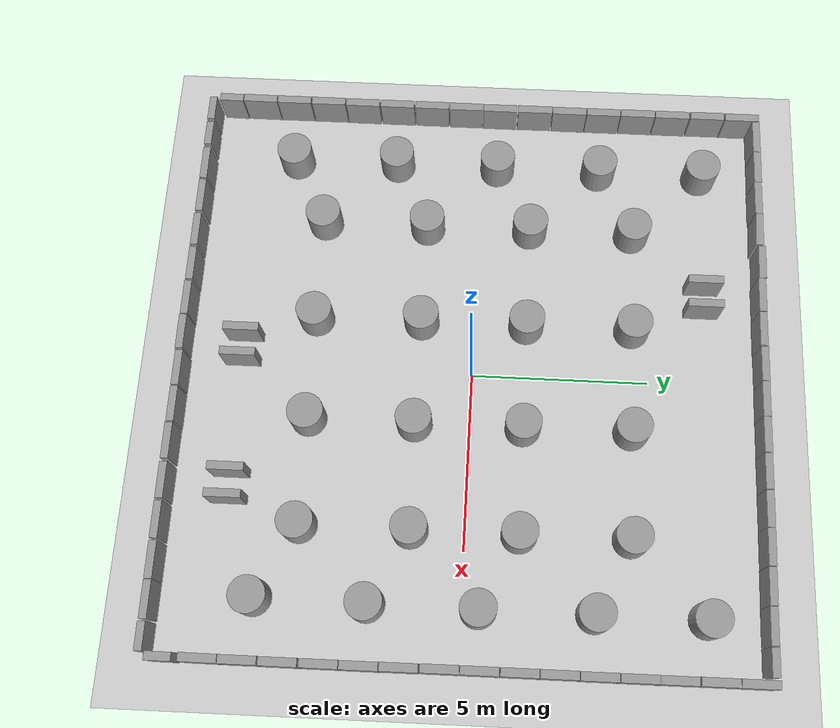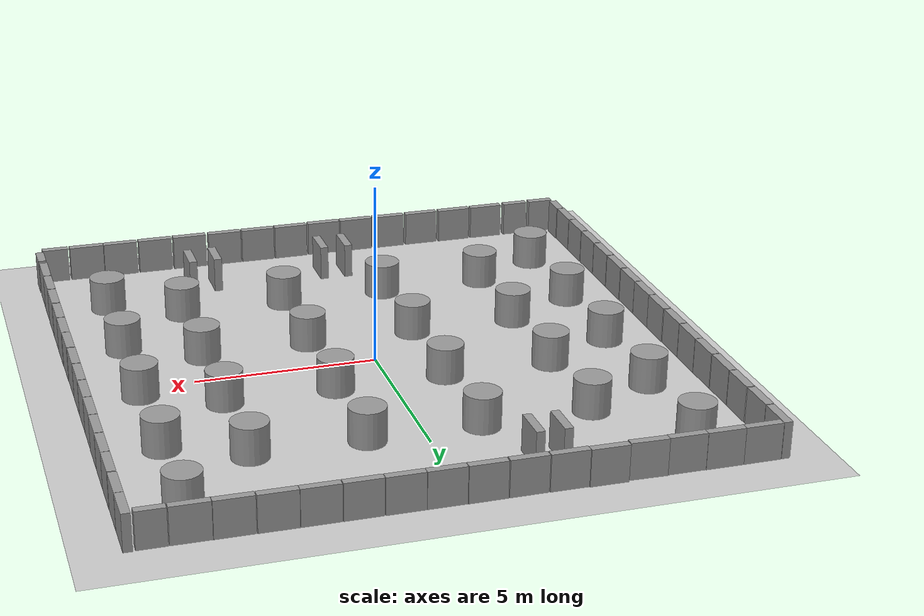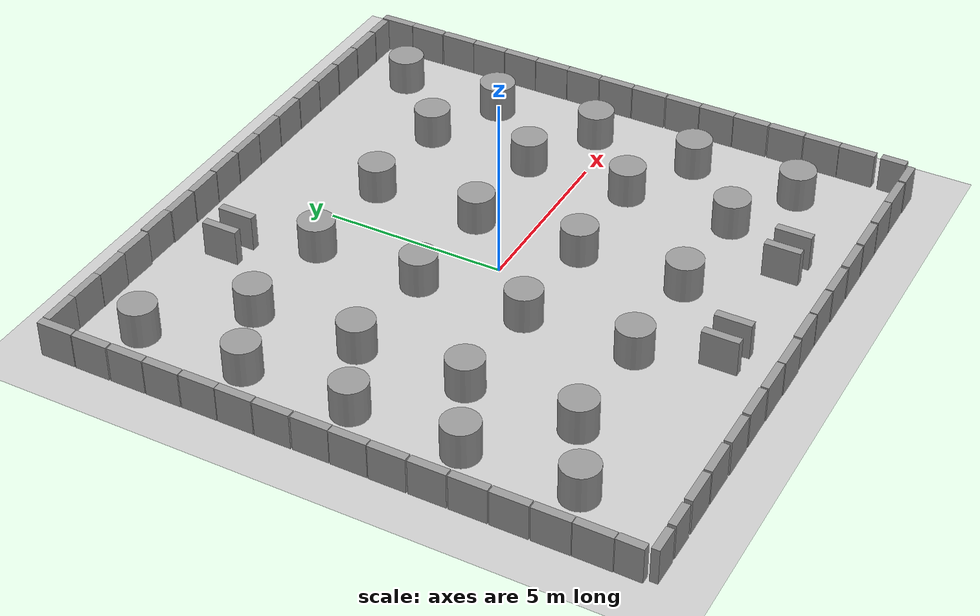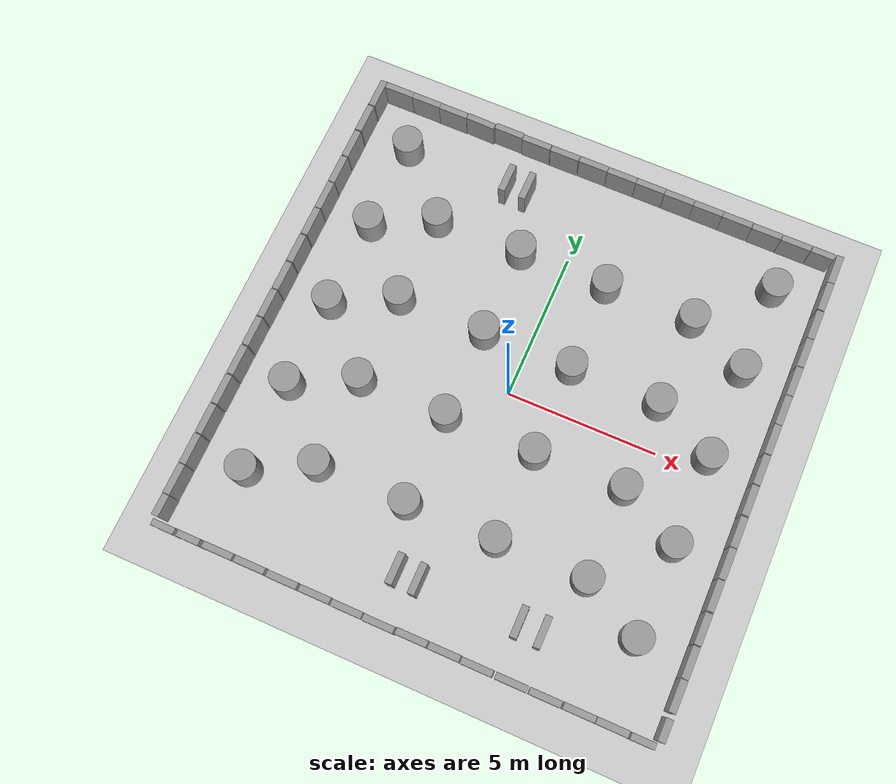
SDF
<sdf version="1.6">
 <world name="default">
  <light name="sun" type="directional">
   <pose>0 0 10 0 -0 0</pose>
   <diffuse>0.8 0.8 0.8 1</diffuse>
   <specular>0.1 0.1 0.1 1</specular>
   <attenuation>
    <range>1000</range>
    <constant>0.9</constant>
    <linear>0.01</linear>
    <quadratic>0.001</quadratic>
   </attenuation>
   <direction>-0.5 0.5 -1</direction>
  </light>
  <model name="ground_plane">
   <static>1</static>
   <static>1</static>
   <link name="link">
    <collision name="collision">
     <geometry><plane><normal>0 0 1</normal><size>100 100</size></plane></geometry>
     <surface><friction><ode><mu>100</mu><mu2>50</mu2></ode></friction></surface>
    </collision>
    <visual name="visual">
     <cast_shadows>0</cast_shadows>
     <geometry><plane><normal>0 0 1</normal><size>100 100</size></plane></geometry>
     <material>
      <script><uri>file://media/materials/scripts/gazebo.material</uri><name>Gazebo/Grey</name></script>
     </material>
    </visual>
   </link>
  </model>
  <gravity>0 0 -9.8</gravity>
  <magnetic_field>6e-06 2.3e-05 -4.2e-05</magnetic_field>
  <atmosphere type="adiabatic"/>
  <physics name="default_physics" default="0" type="ode">
   <max_step_size>0.001</max_step_size>
   <real_time_factor>1</real_time_factor>
   <real_time_update_rate>1000</real_time_update_rate>
  </physics>
  <scene><ambient>0.4 0.4 0.4 1</ambient><background>0.7 0.7 0.7 1</background><shadows>1</shadows></scene>
  <spherical_coordinates>
   <surface_model>EARTH_WGS84</surface_model>
   <latitude_deg>0</latitude_deg>
   <longitude_deg>0</longitude_deg>
   <elevation>0</elevation>
   <heading_deg>0</heading_deg>
  </spherical_coordinates>
  <audio><device>default</device></audio>
  <model name="unit_box_clone">
   <pose>-7.49845 8.11976 0.499999 1e-06 -2e-06 0.000246</pose>
   <link name="link">
    <inertial>
     <mass>1</mass>
     <inertia>
      <ixx>0.166667</ixx>
      <ixy>0</ixy>
      <ixz>0</ixz>
      <iyy>0.166667</iyy>
      <iyz>0</iyz>
      <izz>0.166667</izz>
     </inertia>
    </inertial>
    <collision name="collision"><geometry><box><size>1 0.210541 1</size></box></geometry></collision>
    <visual name="visual">
     <geometry><box><size>1 0.210541 1</size></box></geometry>
     <material>
      <script><name>Gazebo/Grey</name><uri>file://media/materials/scripts/gazebo.material</uri></script>
     </material>
    </visual>
   </link>
  </model>
  <model name="unit_box_clone_0">
   <pose>-6.4973 8.11962 0.499999 1e-06 -2e-06 -0.00236</pose>
   <link name="link">
    <inertial>
     <mass>1</mass>
     <inertia>
      <ixx>0.166667</ixx>
      <ixy>0</ixy>
      <ixz>0</ixz>
      <iyy>0.166667</iyy>
      <iyz>0</iyz>
      <izz>0.166667</izz>
     </inertia>
    </inertial>
    <collision name="collision"><geometry><box><size>1 0.210541 1</size></box></geometry></collision>
    <visual name="visual">
     <geometry><box><size>1 0.210541 1</size></box></geometry>
     <material>
      <script><name>Gazebo/Grey</name><uri>file://media/materials/scripts/gazebo.material</uri></script>
     </material>
    </visual>
   </link>
  </model>
  <model name="unit_box_clone_1">
   <pose>-5.49732 8.10837 0.499999 1e-06 -2e-06 -0.002352</pose>
   <link name="link">
    <inertial>
     <mass>1</mass>
     <inertia>
      <ixx>0.166667</ixx>
      <ixy>0</ixy>
      <ixz>0</ixz>
      <iyy>0.166667</iyy>
      <iyz>0</iyz>
      <izz>0.166667</izz>
     </inertia>
    </inertial>
    <collision name="collision"><geometry><box><size>1 0.210541 1</size></box></geometry></collision>
    <visual name="visual">
     <geometry><box><size>1 0.210541 1</size></box></geometry>
     <material>
      <script><name>Gazebo/Grey</name><uri>file://media/materials/scripts/gazebo.material</uri></script>
     </material>
    </visual>
   </link>
  </model>
  <model name="unit_box_clone_2">
   <pose>-4.49485 8.11079 0.499999 -1e-06 -2e-06 -0.027009</pose>
   <link name="link">
    <inertial>
     <mass>1</mass>
     <inertia>
      <ixx>0.166667</ixx>
      <ixy>0</ixy>
      <ixz>0</ixz>
      <iyy>0.166667</iyy>
      <iyz>0</iyz>
      <izz>0.166667</izz>
     </inertia>
    </inertial>
    <collision name="collision"><geometry><box><size>1 0.210541 1</size></box></geometry></collision>
    <visual name="visual">
     <geometry><box><size>1 0.210541 1</size></box></geometry>
     <material>
      <script><name>Gazebo/Grey</name><uri>file://media/materials/scripts/gazebo.material</uri></script>
     </material>
    </visual>
   </link>
  </model>
  <model name="unit_box_clone_3">
   <pose>-3.46835 8.15036 0.499999 -1e-06 2e-06 -0.007882</pose>
   <link name="link">
    <inertial>
     <mass>1</mass>
     <inertia>
      <ixx>0.166667</ixx>
      <ixy>0</ixy>
      <ixz>0</ixz>
      <iyy>0.166667</iyy>
      <iyz>0</iyz>
      <izz>0.166667</izz>
     </inertia>
    </inertial>
    <collision name="collision"><geometry><box><size>1 0.210541 1</size></box></geometry></collision>
    <visual name="visual">
     <geometry><box><size>1 0.210541 1</size></box></geometry>
     <material>
      <script><name>Gazebo/Grey</name><uri>file://media/materials/scripts/gazebo.material</uri></script>
     </material>
    </visual>
   </link>
  </model>
  <model name="unit_box_clone_4">
   <pose>-2.46316 8.11845 0.499999 1e-06 -2e-06 0.000246</pose>
   <link name="link">
    <inertial>
     <mass>1</mass>
     <inertia>
      <ixx>0.166667</ixx>
      <ixy>0</ixy>
      <ixz>0</ixz>
      <iyy>0.166667</iyy>
      <iyz>0</iyz>
      <izz>0.166667</izz>
     </inertia>
    </inertial>
    <collision name="collision"><geometry><box><size>1 0.210541 1</size></box></geometry></collision>
    <visual name="visual">
     <geometry><box><size>1 0.210541 1</size></box></geometry>
     <material>
      <script><name>Gazebo/Grey</name><uri>file://media/materials/scripts/gazebo.material</uri></script>
     </material>
    </visual>
   </link>
  </model>
  <model name="unit_box_clone_5">
   <pose>-1.44425 8.11179 0.499999 1e-06 -2e-06 0.000246</pose>
   <link name="link">
    <inertial>
     <mass>1</mass>
     <inertia>
      <ixx>0.166667</ixx>
      <ixy>0</ixy>
      <ixz>0</ixz>
      <iyy>0.166667</iyy>
      <iyz>0</iyz>
      <izz>0.166667</izz>
     </inertia>
    </inertial>
    <collision name="collision"><geometry><box><size>1 0.210541 1</size></box></geometry></collision>
    <visual name="visual">
     <geometry><box><size>1 0.210541 1</size></box></geometry>
     <material>
      <script><name>Gazebo/Grey</name><uri>file://media/materials/scripts/gazebo.material</uri></script>
     </material>
    </visual>
   </link>
  </model>
  <model name="unit_box_clone_6">
   <pose>-0.418686 8.11844 0.499999 1e-06 -2e-06 0.000246</pose>
   <link name="link">
    <inertial>
     <mass>1</mass>
     <inertia>
      <ixx>0.166667</ixx>
      <ixy>0</ixy>
      <ixz>0</ixz>
      <iyy>0.166667</iyy>
      <iyz>0</iyz>
      <izz>0.166667</izz>
     </inertia>
    </inertial>
    <collision name="collision"><geometry><box><size>1 0.210541 1</size></box></geometry></collision>
    <visual name="visual">
     <geometry><box><size>1 0.210541 1</size></box></geometry>
     <material>
      <script><name>Gazebo/Grey</name><uri>file://media/materials/scripts/gazebo.material</uri></script>
     </material>
    </visual>
   </link>
  </model>
  <model name="unit_box_clone_7">
   <pose>0.592833 8.11131 0.499999 1e-06 -2e-06 0.000246</pose>
   <link name="link">
    <inertial>
     <mass>1</mass>
     <inertia>
      <ixx>0.166667</ixx>
      <ixy>0</ixy>
      <ixz>0</ixz>
      <iyy>0.166667</iyy>
      <iyz>0</iyz>
      <izz>0.166667</izz>
     </inertia>
    </inertial>
    <collision name="collision"><geometry><box><size>1 0.210541 1</size></box></geometry></collision>
    <visual name="visual">
     <geometry><box><size>1 0.210541 1</size></box></geometry>
     <material>
      <script><name>Gazebo/Grey</name><uri>file://media/materials/scripts/gazebo.material</uri></script>
     </material>
    </visual>
   </link>
  </model>
  <model name="unit_box_clone_8">
   <pose>1.60043 8.10982 0.499999 1e-06 -2e-06 0.000246</pose>
   <link name="link">
    <inertial>
     <mass>1</mass>
     <inertia>
      <ixx>0.166667</ixx>
      <ixy>0</ixy>
      <ixz>0</ixz>
      <iyy>0.166667</iyy>
      <iyz>0</iyz>
      <izz>0.166667</izz>
     </inertia>
    </inertial>
    <collision name="collision"><geometry><box><size>1 0.210541 1</size></box></geometry></collision>
    <visual name="visual">
     <geometry><box><size>1 0.210541 1</size></box></geometry>
     <material>
      <script><name>Gazebo/Grey</name><uri>file://media/materials/scripts/gazebo.material</uri></script>
     </material>
    </visual>
   </link>
  </model>
  <model name="unit_box_clone_9">
   <pose>2.60987 8.10263 0.499999 1e-06 -2e-06 0.000246</pose>
   <link name="link">
    <inertial>
     <mass>1</mass>
     <inertia>
      <ixx>0.166667</ixx>
      <ixy>0</ixy>
      <ixz>0</ixz>
      <iyy>0.166667</iyy>
      <iyz>0</iyz>
      <izz>0.166667</izz>
     </inertia>
    </inertial>
    <collision name="collision"><geometry><box><size>1 0.210541 1</size></box></geometry></collision>
    <visual name="visual">
     <geometry><box><size>1 0.210541 1</size></box></geometry>
     <material>
      <script><name>Gazebo/Grey</name><uri>file://media/materials/scripts/gazebo.material</uri></script>
     </material>
    </visual>
   </link>
  </model>
  <model name="unit_box_clone_10">
   <pose>3.62649 8.09904 0.499999 1e-06 -2e-06 0.000246</pose>
   <link name="link">
    <inertial>
     <mass>1</mass>
     <inertia>
      <ixx>0.166667</ixx>
      <ixy>0</ixy>
      <ixz>0</ixz>
      <iyy>0.166667</iyy>
      <iyz>0</iyz>
      <izz>0.166667</izz>
     </inertia>
    </inertial>
    <collision name="collision"><geometry><box><size>1 0.210541 1</size></box></geometry></collision>
    <visual name="visual">
     <geometry><box><size>1 0.210541 1</size></box></geometry>
     <material>
      <script><name>Gazebo/Grey</name><uri>file://media/materials/scripts/gazebo.material</uri></script>
     </material>
    </visual>
   </link>
  </model>
  <model name="unit_box_clone_11">
   <pose>4.63308 8.09512 0.499999 1e-06 -2e-06 -0.003341</pose>
   <link name="link">
    <inertial>
     <mass>1</mass>
     <inertia>
      <ixx>0.166667</ixx>
      <ixy>0</ixy>
      <ixz>0</ixz>
      <iyy>0.166667</iyy>
      <iyz>0</iyz>
      <izz>0.166667</izz>
     </inertia>
    </inertial>
    <collision name="collision"><geometry><box><size>1 0.210541 1</size></box></geometry></collision>
    <visual name="visual">
     <geometry><box><size>1 0.210541 1</size></box></geometry>
     <material>
      <script><name>Gazebo/Grey</name><uri>file://media/materials/scripts/gazebo.material</uri></script>
     </material>
    </visual>
   </link>
  </model>
  <model name="unit_box_0_clone_0">
   <pose>8.11522 6.68458 0.5 0 0 -0.000202</pose>
   <link name="link">
    <inertial>
     <mass>1</mass>
     <inertia>
      <ixx>0.166667</ixx>
      <ixy>0</ixy>
      <ixz>0</ixz>
      <iyy>0.166667</iyy>
      <iyz>0</iyz>
      <izz>0.166667</izz>
     </inertia>
    </inertial>
    <collision name="collision"><geometry><box><size>0.230819 1 1</size></box></geometry></collision>
    <visual name="visual">
     <geometry><box><size>0.230819 1 1</size></box></geometry>
     <material>
      <script><name>Gazebo/Grey</name><uri>file://media/materials/scripts/gazebo.material</uri></script>
     </material>
    </visual>
   </link>
  </model>
  <model name="unit_box_0_clone_1">
   <pose>8.11915 5.6517 0.5 0 -0 0.000101</pose>
   <link name="link">
    <inertial>
     <mass>1</mass>
     <inertia>
      <ixx>0.166667</ixx>
      <ixy>0</ixy>
      <ixz>0</ixz>
      <iyy>0.166667</iyy>
      <iyz>0</iyz>
      <izz>0.166667</izz>
     </inertia>
    </inertial>
    <collision name="collision"><geometry><box><size>0.230819 1 1</size></box></geometry></collision>
    <visual name="visual">
     <geometry><box><size>0.230819 1 1</size></box></geometry>
     <material>
      <script><name>Gazebo/Grey</name><uri>file://media/materials/scripts/gazebo.material</uri></script>
     </material>
    </visual>
   </link>
  </model>
  <model name="unit_box_0_clone_2">
   <pose>8.11914 4.64016 0.5 0 -0 0.000194</pose>
   <link name="link">
    <inertial>
     <mass>1</mass>
     <inertia>
      <ixx>0.166667</ixx>
      <ixy>0</ixy>
      <ixz>0</ixz>
      <iyy>0.166667</iyy>
      <iyz>0</iyz>
      <izz>0.166667</izz>
     </inertia>
    </inertial>
    <collision name="collision"><geometry><box><size>0.230819 1 1</size></box></geometry></collision>
    <visual name="visual">
     <geometry><box><size>0.230819 1 1</size></box></geometry>
     <material>
      <script><name>Gazebo/Grey</name><uri>file://media/materials/scripts/gazebo.material</uri></script>
     </material>
    </visual>
   </link>
  </model>
  <model name="unit_box_0_clone_3">
   <pose>8.11914 3.62228 0.5 0 -0 0.000175</pose>
   <link name="link">
    <inertial>
     <mass>1</mass>
     <inertia>
      <ixx>0.166667</ixx>
      <ixy>0</ixy>
      <ixz>0</ixz>
      <iyy>0.166667</iyy>
      <iyz>0</iyz>
      <izz>0.166667</izz>
     </inertia>
    </inertial>
    <collision name="collision"><geometry><box><size>0.230819 1 1</size></box></geometry></collision>
    <visual name="visual">
     <geometry><box><size>0.230819 1 1</size></box></geometry>
     <material>
      <script><name>Gazebo/Grey</name><uri>file://media/materials/scripts/gazebo.material</uri></script>
     </material>
    </visual>
   </link>
  </model>
  <model name="unit_box_0_clone_4">
   <pose>8.11332 2.61063 0.5 -1e-06 1e-06 -0.001033</pose>
   <link name="link">
    <inertial>
     <mass>1</mass>
     <inertia>
      <ixx>0.166667</ixx>
      <ixy>0</ixy>
      <ixz>0</ixz>
      <iyy>0.166667</iyy>
      <iyz>0</iyz>
      <izz>0.166667</izz>
     </inertia>
    </inertial>
    <collision name="collision"><geometry><box><size>0.230819 1 1</size></box></geometry></collision>
    <visual name="visual">
     <geometry><box><size>0.230819 1 1</size></box></geometry>
     <material>
      <script><name>Gazebo/Grey</name><uri>file://media/materials/scripts/gazebo.material</uri></script>
     </material>
    </visual>
   </link>
  </model>
  <model name="unit_box_0_clone_5">
   <pose>8.11277 1.59919 0.5 0 -0 0.000175</pose>
   <link name="link">
    <inertial>
     <mass>1</mass>
     <inertia>
      <ixx>0.166667</ixx>
      <ixy>0</ixy>
      <ixz>0</ixz>
      <iyy>0.166667</iyy>
      <iyz>0</iyz>
      <izz>0.166667</izz>
     </inertia>
    </inertial>
    <collision name="collision"><geometry><box><size>0.230819 1 1</size></box></geometry></collision>
    <visual name="visual">
     <geometry><box><size>0.230819 1 1</size></box></geometry>
     <material>
      <script><name>Gazebo/Grey</name><uri>file://media/materials/scripts/gazebo.material</uri></script>
     </material>
    </visual>
   </link>
  </model>
  <model name="unit_box_0_clone_6">
   <pose>8.11277 0.574938 0.5 0 -0 0.000175</pose>
   <link name="link">
    <inertial>
     <mass>1</mass>
     <inertia>
      <ixx>0.166667</ixx>
      <ixy>0</ixy>
      <ixz>0</ixz>
      <iyy>0.166667</iyy>
      <iyz>0</iyz>
      <izz>0.166667</izz>
     </inertia>
    </inertial>
    <collision name="collision"><geometry><box><size>0.230819 1 1</size></box></geometry></collision>
    <visual name="visual">
     <geometry><box><size>0.230819 1 1</size></box></geometry>
     <material>
      <script><name>Gazebo/Grey</name><uri>file://media/materials/scripts/gazebo.material</uri></script>
     </material>
    </visual>
   </link>
  </model>
  <model name="unit_box_0_clone_7">
   <pose>8.11276 -0.44932 0.5 0 -0 0.000175</pose>
   <link name="link">
    <inertial>
     <mass>1</mass>
     <inertia>
      <ixx>0.166667</ixx>
      <ixy>0</ixy>
      <ixz>0</ixz>
      <iyy>0.166667</iyy>
      <iyz>0</iyz>
      <izz>0.166667</izz>
     </inertia>
    </inertial>
    <collision name="collision"><geometry><box><size>0.230819 1 1</size></box></geometry></collision>
    <visual name="visual">
     <geometry><box><size>0.230819 1 1</size></box></geometry>
     <material>
      <script><name>Gazebo/Grey</name><uri>file://media/materials/scripts/gazebo.material</uri></script>
     </material>
    </visual>
   </link>
  </model>
  <model name="unit_box_0_clone_8">
   <pose>8.11912 -1.48629 0.5 0 -0 0.000175</pose>
   <link name="link">
    <inertial>
     <mass>1</mass>
     <inertia>
      <ixx>0.166667</ixx>
      <ixy>0</ixy>
      <ixz>0</ixz>
      <iyy>0.166667</iyy>
      <iyz>0</iyz>
      <izz>0.166667</izz>
     </inertia>
    </inertial>
    <collision name="collision"><geometry><box><size>0.230819 1 1</size></box></geometry></collision>
    <visual name="visual">
     <geometry><box><size>0.230819 1 1</size></box></geometry>
     <material>
      <script><name>Gazebo/Grey</name><uri>file://media/materials/scripts/gazebo.material</uri></script>
     </material>
    </visual>
   </link>
  </model>
  <model name="unit_box_0_clone_9">
   <pose>8.12548 -2.5042 0.5 0 -0 0.000175</pose>
   <link name="link">
    <inertial>
     <mass>1</mass>
     <inertia>
      <ixx>0.166667</ixx>
      <ixy>0</ixy>
      <ixz>0</ixz>
      <iyy>0.166667</iyy>
      <iyz>0</iyz>
      <izz>0.166667</izz>
     </inertia>
    </inertial>
    <collision name="collision"><geometry><box><size>0.230819 1 1</size></box></geometry></collision>
    <visual name="visual">
     <geometry><box><size>0.230819 1 1</size></box></geometry>
     <material>
      <script><name>Gazebo/Grey</name><uri>file://media/materials/scripts/gazebo.material</uri></script>
     </material>
    </visual>
   </link>
  </model>
  <model name="unit_box_0_clone_10">
   <pose>8.12331 -3.52223 0.5 0 -0 0.000175</pose>
   <link name="link">
    <inertial>
     <mass>1</mass>
     <inertia>
      <ixx>0.166667</ixx>
      <ixy>0</ixy>
      <ixz>0</ixz>
      <iyy>0.166667</iyy>
      <iyz>0</iyz>
      <izz>0.166667</izz>
     </inertia>
    </inertial>
    <collision name="collision"><geometry><box><size>0.230819 1 1</size></box></geometry></collision>
    <visual name="visual">
     <geometry><box><size>0.230819 1 1</size></box></geometry>
     <material>
      <script><name>Gazebo/Grey</name><uri>file://media/materials/scripts/gazebo.material</uri></script>
     </material>
    </visual>
   </link>
  </model>
  <model name="unit_box_0_clone_11">
   <pose>8.1233 -4.56316 0.5 0 -0 0.000175</pose>
   <link name="link">
    <inertial>
     <mass>1</mass>
     <inertia>
      <ixx>0.166667</ixx>
      <ixy>0</ixy>
      <ixz>0</ixz>
      <iyy>0.166667</iyy>
      <iyz>0</iyz>
      <izz>0.166667</izz>
     </inertia>
    </inertial>
    <collision name="collision"><geometry><box><size>0.230819 1 1</size></box></geometry></collision>
    <visual name="visual">
     <geometry><box><size>0.230819 1 1</size></box></geometry>
     <material>
      <script><name>Gazebo/Grey</name><uri>file://media/materials/scripts/gazebo.material</uri></script>
     </material>
    </visual>
   </link>
  </model>
  <model name="unit_box_0_clone_12">
   <pose>8.11815 -5.59377 0.5 0 -0 0.000175</pose>
   <link name="link">
    <inertial>
     <mass>1</mass>
     <inertia>
      <ixx>0.166667</ixx>
      <ixy>0</ixy>
      <ixz>0</ixz>
      <iyy>0.166667</iyy>
      <iyz>0</iyz>
      <izz>0.166667</izz>
     </inertia>
    </inertial>
    <collision name="collision"><geometry><box><size>0.230819 1 1</size></box></geometry></collision>
    <visual name="visual">
     <geometry><box><size>0.230819 1 1</size></box></geometry>
     <material>
      <script><name>Gazebo/Grey</name><uri>file://media/materials/scripts/gazebo.material</uri></script>
     </material>
    </visual>
   </link>
  </model>
  <model name="unit_box_0_clone_13">
   <pose>8.11333 -6.60776 0.5 0 0 -0.005331</pose>
   <link name="link">
    <inertial>
     <mass>1</mass>
     <inertia>
      <ixx>0.166667</ixx>
      <ixy>0</ixy>
      <ixz>0</ixz>
      <iyy>0.166667</iyy>
      <iyz>0</iyz>
      <izz>0.166667</izz>
     </inertia>
    </inertial>
    <collision name="collision"><geometry><box><size>0.230819 1 1</size></box></geometry></collision>
    <visual name="visual">
     <geometry><box><size>0.230819 1 1</size></box></geometry>
     <material>
      <script><name>Gazebo/Grey</name><uri>file://media/materials/scripts/gazebo.material</uri></script>
     </material>
    </visual>
   </link>
  </model>
  <model name="unit_box_clone_15_clone_0">
   <pose>6.71207 -8.13128 0.499999 1e-06 -2e-06 0.000246</pose>
   <link name="link">
    <inertial>
     <mass>1</mass>
     <inertia>
      <ixx>0.166667</ixx>
      <ixy>0</ixy>
      <ixz>0</ixz>
      <iyy>0.166667</iyy>
      <iyz>0</iyz>
      <izz>0.166667</izz>
     </inertia>
    </inertial>
    <collision name="collision"><geometry><box><size>1 0.210541 1</size></box></geometry></collision>
    <visual name="visual">
     <geometry><box><size>1 0.210541 1</size></box></geometry>
     <material>
      <script><name>Gazebo/Grey</name><uri>file://media/materials/scripts/gazebo.material</uri></script>
     </material>
    </visual>
   </link>
  </model>
  <model name="unit_box_clone_15_clone_1">
   <pose>5.69715 -8.13127 0.499999 1e-06 -2e-06 0.000246</pose>
   <link name="link">
    <inertial>
     <mass>1</mass>
     <inertia>
      <ixx>0.166667</ixx>
      <ixy>0</ixy>
      <ixz>0</ixz>
      <iyy>0.166667</iyy>
      <iyz>0</iyz>
      <izz>0.166667</izz>
     </inertia>
    </inertial>
    <collision name="collision"><geometry><box><size>1 0.210541 1</size></box></geometry></collision>
    <visual name="visual">
     <geometry><box><size>1 0.210541 1</size></box></geometry>
     <material>
      <script><name>Gazebo/Grey</name><uri>file://media/materials/scripts/gazebo.material</uri></script>
     </material>
    </visual>
   </link>
  </model>
  <model name="unit_box_clone_15_clone_2">
   <pose>4.63881 -8.13745 0.499999 1e-06 -2e-06 0.000246</pose>
   <link name="link">
    <inertial>
     <mass>1</mass>
     <inertia>
      <ixx>0.166667</ixx>
      <ixy>0</ixy>
      <ixz>0</ixz>
      <iyy>0.166667</iyy>
      <iyz>0</iyz>
      <izz>0.166667</izz>
     </inertia>
    </inertial>
    <collision name="collision"><geometry><box><size>1 0.210541 1</size></box></geometry></collision>
    <visual name="visual">
     <geometry><box><size>1 0.210541 1</size></box></geometry>
     <material>
      <script><name>Gazebo/Grey</name><uri>file://media/materials/scripts/gazebo.material</uri></script>
     </material>
    </visual>
   </link>
  </model>
  <model name="unit_box_clone_15_clone_3">
   <pose>3.57975 -8.13745 0.499999 1e-06 -2e-06 0.000246</pose>
   <link name="link">
    <inertial>
     <mass>1</mass>
     <inertia>
      <ixx>0.166667</ixx>
      <ixy>0</ixy>
      <ixz>0</ixz>
      <iyy>0.166667</iyy>
      <iyz>0</iyz>
      <izz>0.166667</izz>
     </inertia>
    </inertial>
    <collision name="collision"><geometry><box><size>1 0.210541 1</size></box></geometry></collision>
    <visual name="visual">
     <geometry><box><size>1 0.210541 1</size></box></geometry>
     <material>
      <script><name>Gazebo/Grey</name><uri>file://media/materials/scripts/gazebo.material</uri></script>
     </material>
    </visual>
   </link>
  </model>
  <model name="unit_box_clone_15_clone_4">
   <pose>2.49815 -8.13744 0.499999 1e-06 -2e-06 0.000246</pose>
   <link name="link">
    <inertial>
     <mass>1</mass>
     <inertia>
      <ixx>0.166667</ixx>
      <ixy>0</ixy>
      <ixz>0</ixz>
      <iyy>0.166667</iyy>
      <iyz>0</iyz>
      <izz>0.166667</izz>
     </inertia>
    </inertial>
    <collision name="collision"><geometry><box><size>1 0.210541 1</size></box></geometry></collision>
    <visual name="visual">
     <geometry><box><size>1 0.210541 1</size></box></geometry>
     <material>
      <script><name>Gazebo/Grey</name><uri>file://media/materials/scripts/gazebo.material</uri></script>
     </material>
    </visual>
   </link>
  </model>
  <model name="unit_box_clone_15_clone_5">
   <pose>1.46162 -8.12617 0.499999 1e-06 -2e-06 0.000246</pose>
   <link name="link">
    <inertial>
     <mass>1</mass>
     <inertia>
      <ixx>0.166667</ixx>
      <ixy>0</ixy>
      <ixz>0</ixz>
      <iyy>0.166667</iyy>
      <iyz>0</iyz>
      <izz>0.166667</izz>
     </inertia>
    </inertial>
    <collision name="collision"><geometry><box><size>1 0.210541 1</size></box></geometry></collision>
    <visual name="visual">
     <geometry><box><size>1 0.210541 1</size></box></geometry>
     <material>
      <script><name>Gazebo/Grey</name><uri>file://media/materials/scripts/gazebo.material</uri></script>
     </material>
    </visual>
   </link>
  </model>
  <model name="unit_box_clone_15_clone_6">
   <pose>0.425086 -8.12616 0.499999 1e-06 -2e-06 0.000246</pose>
   <link name="link">
    <inertial>
     <mass>1</mass>
     <inertia>
      <ixx>0.166667</ixx>
      <ixy>0</ixy>
      <ixz>0</ixz>
      <iyy>0.166667</iyy>
      <iyz>0</iyz>
      <izz>0.166667</izz>
     </inertia>
    </inertial>
    <collision name="collision"><geometry><box><size>1 0.210541 1</size></box></geometry></collision>
    <visual name="visual">
     <geometry><box><size>1 0.210541 1</size></box></geometry>
     <material>
      <script><name>Gazebo/Grey</name><uri>file://media/materials/scripts/gazebo.material</uri></script>
     </material>
    </visual>
   </link>
  </model>
  <model name="unit_box_clone_15_clone_7">
   <pose>-0.633976 -8.14871 0.499999 1e-06 -2e-06 0.000246</pose>
   <link name="link">
    <inertial>
     <mass>1</mass>
     <inertia>
      <ixx>0.166667</ixx>
      <ixy>0</ixy>
      <ixz>0</ixz>
      <iyy>0.166667</iyy>
      <iyz>0</iyz>
      <izz>0.166667</izz>
     </inertia>
    </inertial>
    <collision name="collision"><geometry><box><size>1 0.210541 1</size></box></geometry></collision>
    <visual name="visual">
     <geometry><box><size>1 0.210541 1</size></box></geometry>
     <material>
      <script><name>Gazebo/Grey</name><uri>file://media/materials/scripts/gazebo.material</uri></script>
     </material>
    </visual>
   </link>
  </model>
  <model name="unit_box_clone_15_clone_8">
   <pose>-1.65923 -8.13743 0.499999 1e-06 -2e-06 0.000246</pose>
   <link name="link">
    <inertial>
     <mass>1</mass>
     <inertia>
      <ixx>0.166667</ixx>
      <ixy>0</ixy>
      <ixz>0</ixz>
      <iyy>0.166667</iyy>
      <iyz>0</iyz>
      <izz>0.166667</izz>
     </inertia>
    </inertial>
    <collision name="collision"><geometry><box><size>1 0.210541 1</size></box></geometry></collision>
    <visual name="visual">
     <geometry><box><size>1 0.210541 1</size></box></geometry>
     <material>
      <script><name>Gazebo/Grey</name><uri>file://media/materials/scripts/gazebo.material</uri></script>
     </material>
    </visual>
   </link>
  </model>
  <model name="unit_box_clone_15_clone_9">
   <pose>-2.70703 -8.12618 0.499999 1e-06 -2e-06 0.000246</pose>
   <link name="link">
    <inertial>
     <mass>1</mass>
     <inertia>
      <ixx>0.166667</ixx>
      <ixy>0</ixy>
      <ixz>0</ixz>
      <iyy>0.166667</iyy>
      <iyz>0</iyz>
      <izz>0.166667</izz>
     </inertia>
    </inertial>
    <collision name="collision"><geometry><box><size>1 0.210541 1</size></box></geometry></collision>
    <visual name="visual">
     <geometry><box><size>1 0.210541 1</size></box></geometry>
     <material>
      <script><name>Gazebo/Grey</name><uri>file://media/materials/scripts/gazebo.material</uri></script>
     </material>
    </visual>
   </link>
  </model>
  <model name="unit_box_clone_15_clone_10">
   <pose>-3.77736 -8.12617 0.499999 1e-06 -2e-06 0.000246</pose>
   <link name="link">
    <inertial>
     <mass>1</mass>
     <inertia>
      <ixx>0.166667</ixx>
      <ixy>0</ixy>
      <ixz>0</ixz>
      <iyy>0.166667</iyy>
      <iyz>0</iyz>
      <izz>0.166667</izz>
     </inertia>
    </inertial>
    <collision name="collision"><geometry><box><size>1 0.210541 1</size></box></geometry></collision>
    <visual name="visual">
     <geometry><box><size>1 0.210541 1</size></box></geometry>
     <material>
      <script><name>Gazebo/Grey</name><uri>file://media/materials/scripts/gazebo.material</uri></script>
     </material>
    </visual>
   </link>
  </model>
  <model name="unit_box_clone_15_clone_11">
   <pose>-4.85896 -8.11491 0.499999 1e-06 -2e-06 0.000246</pose>
   <link name="link">
    <inertial>
     <mass>1</mass>
     <inertia>
      <ixx>0.166667</ixx>
      <ixy>0</ixy>
      <ixz>0</ixz>
      <iyy>0.166667</iyy>
      <iyz>0</iyz>
      <izz>0.166667</izz>
     </inertia>
    </inertial>
    <collision name="collision"><geometry><box><size>1 0.210541 1</size></box></geometry></collision>
    <visual name="visual">
     <geometry><box><size>1 0.210541 1</size></box></geometry>
     <material>
      <script><name>Gazebo/Grey</name><uri>file://media/materials/scripts/gazebo.material</uri></script>
     </material>
    </visual>
   </link>
  </model>
  <model name="unit_box_clone_15_clone_12">
   <pose>-5.91802 -8.1149 0.499999 1e-06 -2e-06 0.000246</pose>
   <link name="link">
    <inertial>
     <mass>1</mass>
     <inertia>
      <ixx>0.166667</ixx>
      <ixy>0</ixy>
      <ixz>0</ixz>
      <iyy>0.166667</iyy>
      <iyz>0</iyz>
      <izz>0.166667</izz>
     </inertia>
    </inertial>
    <collision name="collision"><geometry><box><size>1 0.210541 1</size></box></geometry></collision>
    <visual name="visual">
     <geometry><box><size>1 0.210541 1</size></box></geometry>
     <material>
      <script><name>Gazebo/Grey</name><uri>file://media/materials/scripts/gazebo.material</uri></script>
     </material>
    </visual>
   </link>
  </model>
  <model name="unit_box_0_clone_4_clone">
   <pose>-8.12647 7.71769 0.5 0 -0 0.000175</pose>
   <link name="link">
    <inertial>
     <mass>1</mass>
     <inertia>
      <ixx>0.166667</ixx>
      <ixy>0</ixy>
      <ixz>0</ixz>
      <iyy>0.166667</iyy>
      <iyz>0</iyz>
      <izz>0.166667</izz>
     </inertia>
    </inertial>
    <collision name="collision"><geometry><box><size>0.230819 1 1</size></box></geometry></collision>
    <visual name="visual">
     <geometry><box><size>0.230819 1 1</size></box></geometry>
     <material>
      <script><name>Gazebo/Grey</name><uri>file://media/materials/scripts/gazebo.material</uri></script>
     </material>
    </visual>
   </link>
  </model>
  <model name="unit_box_0_clone_4_clone_0">
   <pose>-8.13281 6.68715 0.5 0 -0 0.000175</pose>
   <link name="link">
    <inertial>
     <mass>1</mass>
     <inertia>
      <ixx>0.166667</ixx>
      <ixy>0</ixy>
      <ixz>0</ixz>
      <iyy>0.166667</iyy>
      <iyz>0</iyz>
      <izz>0.166667</izz>
     </inertia>
    </inertial>
    <collision name="collision"><geometry><box><size>0.230819 1 1</size></box></geometry></collision>
    <visual name="visual">
     <geometry><box><size>0.230819 1 1</size></box></geometry>
     <material>
      <script><name>Gazebo/Grey</name><uri>file://media/materials/scripts/gazebo.material</uri></script>
     </material>
    </visual>
   </link>
  </model>
  <model name="unit_box_0_clone_4_clone_1">
   <pose>-8.12606 5.64722 0.5 0 -0 0.000175</pose>
   <link name="link">
    <inertial>
     <mass>1</mass>
     <inertia>
      <ixx>0.166667</ixx>
      <ixy>0</ixy>
      <ixz>0</ixz>
      <iyy>0.166667</iyy>
      <iyz>0</iyz>
      <izz>0.166667</izz>
     </inertia>
    </inertial>
    <collision name="collision"><geometry><box><size>0.230819 1 1</size></box></geometry></collision>
    <visual name="visual">
     <geometry><box><size>0.230819 1 1</size></box></geometry>
     <material>
      <script><name>Gazebo/Grey</name><uri>file://media/materials/scripts/gazebo.material</uri></script>
     </material>
    </visual>
   </link>
  </model>
  <model name="unit_box_0_clone_4_clone_2">
   <pose>-8.12607 4.6208 0.5 0 -0 0.000175</pose>
   <link name="link">
    <inertial>
     <mass>1</mass>
     <inertia>
      <ixx>0.166667</ixx>
      <ixy>0</ixy>
      <ixz>0</ixz>
      <iyy>0.166667</iyy>
      <iyz>0</iyz>
      <izz>0.166667</izz>
     </inertia>
    </inertial>
    <collision name="collision"><geometry><box><size>0.230819 1 1</size></box></geometry></collision>
    <visual name="visual">
     <geometry><box><size>0.230819 1 1</size></box></geometry>
     <material>
      <script><name>Gazebo/Grey</name><uri>file://media/materials/scripts/gazebo.material</uri></script>
     </material>
    </visual>
   </link>
  </model>
  <model name="unit_box_0_clone_4_clone_3">
   <pose>-8.11932 3.59437 0.5 0 -0 0.000175</pose>
   <link name="link">
    <inertial>
     <mass>1</mass>
     <inertia>
      <ixx>0.166667</ixx>
      <ixy>0</ixy>
      <ixz>0</ixz>
      <iyy>0.166667</iyy>
      <iyz>0</iyz>
      <izz>0.166667</izz>
     </inertia>
    </inertial>
    <collision name="collision"><geometry><box><size>0.230819 1 1</size></box></geometry></collision>
    <visual name="visual">
     <geometry><box><size>0.230819 1 1</size></box></geometry>
     <material>
      <script><name>Gazebo/Grey</name><uri>file://media/materials/scripts/gazebo.material</uri></script>
     </material>
    </visual>
   </link>
  </model>
  <model name="unit_box_0_clone_4_clone_4">
   <pose>-8.11932 2.57471 0.5 0 -0 0.000175</pose>
   <link name="link">
    <inertial>
     <mass>1</mass>
     <inertia>
      <ixx>0.166667</ixx>
      <ixy>0</ixy>
      <ixz>0</ixz>
      <iyy>0.166667</iyy>
      <iyz>0</iyz>
      <izz>0.166667</izz>
     </inertia>
    </inertial>
    <collision name="collision"><geometry><box><size>0.230819 1 1</size></box></geometry></collision>
    <visual name="visual">
     <geometry><box><size>0.230819 1 1</size></box></geometry>
     <material>
      <script><name>Gazebo/Grey</name><uri>file://media/materials/scripts/gazebo.material</uri></script>
     </material>
    </visual>
   </link>
  </model>
  <model name="unit_box_0_clone_4_clone_5">
   <pose>-8.12608 1.54157 0.5 0 -0 0.000175</pose>
   <link name="link">
    <inertial>
     <mass>1</mass>
     <inertia>
      <ixx>0.166667</ixx>
      <ixy>0</ixy>
      <ixz>0</ixz>
      <iyy>0.166667</iyy>
      <iyz>0</iyz>
      <izz>0.166667</izz>
     </inertia>
    </inertial>
    <collision name="collision"><geometry><box><size>0.230819 1 1</size></box></geometry></collision>
    <visual name="visual">
     <geometry><box><size>0.230819 1 1</size></box></geometry>
     <material>
      <script><name>Gazebo/Grey</name><uri>file://media/materials/scripts/gazebo.material</uri></script>
     </material>
    </visual>
   </link>
  </model>
  <model name="unit_box_0_clone_4_clone_6">
   <pose>-8.11933 0.50163 0.5 0 -0 0.000175</pose>
   <link name="link">
    <inertial>
     <mass>1</mass>
     <inertia>
      <ixx>0.166667</ixx>
      <ixy>0</ixy>
      <ixz>0</ixz>
      <iyy>0.166667</iyy>
      <iyz>0</iyz>
      <izz>0.166667</izz>
     </inertia>
    </inertial>
    <collision name="collision"><geometry><box><size>0.230819 1 1</size></box></geometry></collision>
    <visual name="visual">
     <geometry><box><size>0.230819 1 1</size></box></geometry>
     <material>
      <script><name>Gazebo/Grey</name><uri>file://media/materials/scripts/gazebo.material</uri></script>
     </material>
    </visual>
   </link>
  </model>
  <model name="unit_box_0_clone_4_clone_7">
   <pose>-8.12609 -0.518034 0.5 0 -0 0.000175</pose>
   <link name="link">
    <inertial>
     <mass>1</mass>
     <inertia>
      <ixx>0.166667</ixx>
      <ixy>0</ixy>
      <ixz>0</ixz>
      <iyy>0.166667</iyy>
      <iyz>0</iyz>
      <izz>0.166667</izz>
     </inertia>
    </inertial>
    <collision name="collision"><geometry><box><size>0.230819 1 1</size></box></geometry></collision>
    <visual name="visual">
     <geometry><box><size>0.230819 1 1</size></box></geometry>
     <material>
      <script><name>Gazebo/Grey</name><uri>file://media/materials/scripts/gazebo.material</uri></script>
     </material>
    </visual>
   </link>
  </model>
  <model name="unit_box_0_clone_4_clone_8">
   <pose>-8.13284 -1.54445 0.5 0 -0 0.000175</pose>
   <link name="link">
    <inertial>
     <mass>1</mass>
     <inertia>
      <ixx>0.166667</ixx>
      <ixy>0</ixy>
      <ixz>0</ixz>
      <iyy>0.166667</iyy>
      <iyz>0</iyz>
      <izz>0.166667</izz>
     </inertia>
    </inertial>
    <collision name="collision"><geometry><box><size>0.230819 1 1</size></box></geometry></collision>
    <visual name="visual">
     <geometry><box><size>0.230819 1 1</size></box></geometry>
     <material>
      <script><name>Gazebo/Grey</name><uri>file://media/materials/scripts/gazebo.material</uri></script>
     </material>
    </visual>
   </link>
  </model>
  <model name="unit_box_0_clone_4_clone_9">
   <pose>-8.13285 -2.58439 0.5 0 -0 0.000175</pose>
   <link name="link">
    <inertial>
     <mass>1</mass>
     <inertia>
      <ixx>0.166667</ixx>
      <ixy>0</ixy>
      <ixz>0</ixz>
      <iyy>0.166667</iyy>
      <iyz>0</iyz>
      <izz>0.166667</izz>
     </inertia>
    </inertial>
    <collision name="collision"><geometry><box><size>0.230819 1 1</size></box></geometry></collision>
    <visual name="visual">
     <geometry><box><size>0.230819 1 1</size></box></geometry>
     <material>
      <script><name>Gazebo/Grey</name><uri>file://media/materials/scripts/gazebo.material</uri></script>
     </material>
    </visual>
   </link>
  </model>
  <model name="unit_box_0_clone_4_clone_10">
   <pose>-8.13285 -3.62431 0.5 0 -0 0.000175</pose>
   <link name="link">
    <inertial>
     <mass>1</mass>
     <inertia>
      <ixx>0.166667</ixx>
      <ixy>0</ixy>
      <ixz>0</ixz>
      <iyy>0.166667</iyy>
      <iyz>0</iyz>
      <izz>0.166667</izz>
     </inertia>
    </inertial>
    <collision name="collision"><geometry><box><size>0.230819 1 1</size></box></geometry></collision>
    <visual name="visual">
     <geometry><box><size>0.230819 1 1</size></box></geometry>
     <material>
      <script><name>Gazebo/Grey</name><uri>file://media/materials/scripts/gazebo.material</uri></script>
     </material>
    </visual>
   </link>
  </model>
  <model name="unit_box_0_clone_4_clone_11">
   <pose>-8.1396 -4.65747 0.5 0 -0 0.000175</pose>
   <link name="link">
    <inertial>
     <mass>1</mass>
     <inertia>
      <ixx>0.166667</ixx>
      <ixy>0</ixy>
      <ixz>0</ixz>
      <iyy>0.166667</iyy>
      <iyz>0</iyz>
      <izz>0.166667</izz>
     </inertia>
    </inertial>
    <collision name="collision"><geometry><box><size>0.230819 1 1</size></box></geometry></collision>
    <visual name="visual">
     <geometry><box><size>0.230819 1 1</size></box></geometry>
     <material>
      <script><name>Gazebo/Grey</name><uri>file://media/materials/scripts/gazebo.material</uri></script>
     </material>
    </visual>
   </link>
  </model>
  <model name="unit_box_0_clone_4_clone_12">
   <pose>-8.1396 -5.69064 0.5 0 -0 0.000175</pose>
   <link name="link">
    <inertial>
     <mass>1</mass>
     <inertia>
      <ixx>0.166667</ixx>
      <ixy>0</ixy>
      <ixz>0</ixz>
      <iyy>0.166667</iyy>
      <iyz>0</iyz>
      <izz>0.166667</izz>
     </inertia>
    </inertial>
    <collision name="collision"><geometry><box><size>0.230819 1 1</size></box></geometry></collision>
    <visual name="visual">
     <geometry><box><size>0.230819 1 1</size></box></geometry>
     <material>
      <script><name>Gazebo/Grey</name><uri>file://media/materials/scripts/gazebo.material</uri></script>
     </material>
    </visual>
   </link>
  </model>
  <model name="unit_box_0_clone_4_clone_13">
   <pose>-8.14113 -6.70874 0.5 0 0 -0.008698</pose>
   <link name="link">
    <inertial>
     <mass>1</mass>
     <inertia>
      <ixx>0.166667</ixx>
      <ixy>0</ixy>
      <ixz>0</ixz>
      <iyy>0.166667</iyy>
      <iyz>0</iyz>
      <izz>0.166667</izz>
     </inertia>
    </inertial>
    <collision name="collision"><geometry><box><size>0.230819 1 1</size></box></geometry></collision>
    <visual name="visual">
     <geometry><box><size>0.230819 1 1</size></box></geometry>
     <material>
      <script><name>Gazebo/Grey</name><uri>file://media/materials/scripts/gazebo.material</uri></script>
     </material>
    </visual>
   </link>
  </model>
  <model name="unit_box_0_clone_0_clone">
   <pose>8.11438 7.69322 0.5 0 -0 8.3e-05</pose>
   <link name="link">
    <inertial>
     <mass>1</mass>
     <inertia>
      <ixx>0.166667</ixx>
      <ixy>0</ixy>
      <ixz>0</ixz>
      <iyy>0.166667</iyy>
      <iyz>0</iyz>
      <izz>0.166667</izz>
     </inertia>
    </inertial>
    <collision name="collision"><geometry><box><size>0.230819 1 1</size></box></geometry></collision>
    <visual name="visual">
     <geometry><box><size>0.230819 1 1</size></box></geometry>
     <material>
      <script><name>Gazebo/Grey</name><uri>file://media/materials/scripts/gazebo.material</uri></script>
     </material>
    </visual>
   </link>
  </model>
  <model name="unit_box_clone_11_clone">
   <pose>5.6544 8.08381 0.499999 -1e-06 2e-06 -0.003006</pose>
   <link name="link">
    <inertial>
     <mass>1</mass>
     <inertia>
      <ixx>0.166667</ixx>
      <ixy>0</ixy>
      <ixz>0</ixz>
      <iyy>0.166667</iyy>
      <iyz>0</iyz>
      <izz>0.166667</izz>
     </inertia>
    </inertial>
    <collision name="collision"><geometry><box><size>1 0.210541 1</size></box></geometry></collision>
    <visual name="visual">
     <geometry><box><size>1 0.210541 1</size></box></geometry>
     <material>
      <script><name>Gazebo/Grey</name><uri>file://media/materials/scripts/gazebo.material</uri></script>
     </material>
    </visual>
   </link>
  </model>
  <model name="unit_box_clone_11_clone_0">
   <pose>6.66438 8.07331 0.499999 1e-06 -2e-06 -0.003263</pose>
   <link name="link">
    <inertial>
     <mass>1</mass>
     <inertia>
      <ixx>0.166667</ixx>
      <ixy>0</ixy>
      <ixz>0</ixz>
      <iyy>0.166667</iyy>
      <iyz>0</iyz>
      <izz>0.166667</izz>
     </inertia>
    </inertial>
    <collision name="collision"><geometry><box><size>1 0.210541 1</size></box></geometry></collision>
    <visual name="visual">
     <geometry><box><size>1 0.210541 1</size></box></geometry>
     <material>
      <script><name>Gazebo/Grey</name><uri>file://media/materials/scripts/gazebo.material</uri></script>
     </material>
    </visual>
   </link>
  </model>
  <model name="unit_box_clone_11_clone_1_clone">
   <pose>7.56439 8.07324 0.499997 -3e-06 7e-06 -0.004063</pose>
   <link name="link">
    <inertial>
     <mass>1</mass>
     <inertia>
      <ixx>0.166667</ixx>
      <ixy>0</ixy>
      <ixz>0</ixz>
      <iyy>0.166667</iyy>
      <iyz>0</iyz>
      <izz>0.166667</izz>
     </inertia>
    </inertial>
    <collision name="collision"><geometry><box><size>0.750223 0.210541 1</size></box></geometry></collision>
    <visual name="visual">
     <geometry><box><size>0.750223 0.210541 1</size></box></geometry>
     <material>
      <script><name>Gazebo/Grey</name><uri>file://media/materials/scripts/gazebo.material</uri></script>
     </material>
    </visual>
   </link>
  </model>
  <model name="unit_box_clone_11_clone_1_clone_0">
   <pose>-6.90881 -8.11956 0.499997 -2e-06 -8e-06 -0.003491</pose>
   <link name="link">
    <inertial>
     <mass>1</mass>
     <inertia>
      <ixx>0.166667</ixx>
      <ixy>0</ixy>
      <ixz>0</ixz>
      <iyy>0.166667</iyy>
      <iyz>0</iyz>
      <izz>0.166667</izz>
     </inertia>
    </inertial>
    <collision name="collision"><geometry><box><size>0.750223 0.210541 1</size></box></geometry></collision>
    <visual name="visual">
     <geometry><box><size>0.750223 0.210541 1</size></box></geometry>
     <material>
      <script><name>Gazebo/Grey</name><uri>file://media/materials/scripts/gazebo.material</uri></script>
     </material>
    </visual>
   </link>
  </model>
  <model name="unit_box_0_clone_4_clone_13_clone_clone">
   <pose>-8.13833 -7.57661 0.499998 7e-06 1e-06 -0.016612</pose>
   <link name="link">
    <inertial>
     <mass>1</mass>
     <inertia>
      <ixx>0.166667</ixx>
      <ixy>0</ixy>
      <ixz>0</ixz>
      <iyy>0.166667</iyy>
      <iyz>0</iyz>
      <izz>0.166667</izz>
     </inertia>
    </inertial>
    <collision name="collision"><geometry><box><size>0.230819 0.700336 1</size></box></geometry></collision>
    <visual name="visual">
     <geometry><box><size>0.230819 0.700336 1</size></box></geometry>
     <material>
      <script><name>Gazebo/Grey</name><uri>file://media/materials/scripts/gazebo.material</uri></script>
     </material>
    </visual>
   </link>
  </model>
  <model name="unit_box_clone_11_clone_1_clone_0_clone">
   <pose>-7.75475 -8.12201 0.499997 -2e-06 -8e-06 -0.006166</pose>
   <link name="link">
    <inertial>
     <mass>1</mass>
     <inertia>
      <ixx>0.166667</ixx>
      <ixy>0</ixy>
      <ixz>0</ixz>
      <iyy>0.166667</iyy>
      <iyz>0</iyz>
      <izz>0.166667</izz>
     </inertia>
    </inertial>
    <collision name="collision"><geometry><box><size>0.750223 0.210541 1</size></box></geometry></collision>
    <visual name="visual">
     <geometry><box><size>0.750223 0.210541 1</size></box></geometry>
     <material>
      <script><name>Gazebo/Grey</name><uri>file://media/materials/scripts/gazebo.material</uri></script>
     </material>
    </visual>
   </link>
  </model>
  <model name="unit_box_clone_11_clone_1_clone_2">
   <pose>7.64249 -8.13928 0.499997 2e-06 8e-06 0.001957</pose>
   <link name="link">
    <inertial>
     <mass>1</mass>
     <inertia>
      <ixx>0.166667</ixx>
      <ixy>0</ixy>
      <ixz>0</ixz>
      <iyy>0.166667</iyy>
      <iyz>0</iyz>
      <izz>0.166667</izz>
     </inertia>
    </inertial>
    <collision name="collision"><geometry><box><size>0.750223 0.210541 1</size></box></geometry></collision>
    <visual name="visual">
     <geometry><box><size>0.750223 0.210541 1</size></box></geometry>
     <material>
      <script><name>Gazebo/Grey</name><uri>file://media/materials/scripts/gazebo.material</uri></script>
     </material>
    </visual>
   </link>
  </model>
  <model name="unit_box_0_clone_4_clone_13_clone_clone_clone">
   <pose>8.11858 -7.62155 0.499997 -7e-06 2e-06 -0.005397</pose>
   <link name="link">
    <inertial>
     <mass>1</mass>
     <inertia>
      <ixx>0.166667</ixx>
      <ixy>0</ixy>
      <ixz>0</ixz>
      <iyy>0.166667</iyy>
      <iyz>0</iyz>
      <izz>0.166667</izz>
     </inertia>
    </inertial>
    <collision name="collision"><geometry><box><size>0.230819 0.700336 1</size></box></geometry></collision>
    <visual name="visual">
     <geometry><box><size>0.230819 0.700336 1</size></box></geometry>
     <material>
      <script><name>Gazebo/Grey</name><uri>file://media/materials/scripts/gazebo.material</uri></script>
     </material>
    </visual>
   </link>
  </model>
  <model name="unit_cylinder_clone_0_clone">
   <pose>1.52056 1.49925 0.499993 -3e-06 -1e-06 -0</pose>
   <link name="link">
    <inertial>
     <mass>1</mass>
     <inertia><ixx>0.145833</ixx><ixy>0</ixy><ixz>0</ixz><iyy>0.145833</iyy><iyz>0</iyz><izz>0.125</izz></inertia>
    </inertial>
    <collision name="collision">
     <geometry><cylinder><radius>0.5</radius><length>1</length></cylinder></geometry>
    </collision>
    <visual name="visual">
     <geometry><cylinder><radius>0.5</radius><length>1</length></cylinder></geometry>
     <material>
      <script><name>Gazebo/Grey</name><uri>file://media/materials/scripts/gazebo.material</uri></script>
     </material>
    </visual>
   </link>
  </model>
  <model name="unit_cylinder_clone_0_clone_clone">
   <pose>-1.50519 1.50185 0.499997 3e-06 2e-06 0</pose>
   <link name="link">
    <inertial>
     <mass>1</mass>
     <inertia><ixx>0.145833</ixx><ixy>0</ixy><ixz>0</ixz><iyy>0.145833</iyy><iyz>0</iyz><izz>0.125</izz></inertia>
    </inertial>
    <collision name="collision">
     <geometry><cylinder><radius>0.5</radius><length>1</length></cylinder></geometry>
    </collision>
    <visual name="visual">
     <geometry><cylinder><radius>0.5</radius><length>1</length></cylinder></geometry>
     <material>
      <script><name>Gazebo/Grey</name><uri>file://media/materials/scripts/gazebo.material</uri></script>
     </material>
    </visual>
   </link>
  </model>
  <model name="unit_cylinder_clone_0_clone_clone_0">
   <pose>-1.50521 -1.49381 0.499994 -3e-06 -2e-06 0</pose>
   <link name="link">
    <inertial>
     <mass>1</mass>
     <inertia><ixx>0.145833</ixx><ixy>0</ixy><ixz>0</ixz><iyy>0.145833</iyy><iyz>0</iyz><izz>0.125</izz></inertia>
    </inertial>
    <collision name="collision">
     <geometry><cylinder><radius>0.5</radius><length>1</length></cylinder></geometry>
    </collision>
    <visual name="visual">
     <geometry><cylinder><radius>0.5</radius><length>1</length></cylinder></geometry>
     <material>
      <script><name>Gazebo/Grey</name><uri>file://media/materials/scripts/gazebo.material</uri></script>
     </material>
    </visual>
   </link>
  </model>
  <model name="unit_cylinder_clone_0_clone_clone_1">
   <pose>1.51857 -1.52195 0.499997 4e-06 2e-06 -0</pose>
   <link name="link">
    <inertial>
     <mass>1</mass>
     <inertia><ixx>0.145833</ixx><ixy>0</ixy><ixz>0</ixz><iyy>0.145833</iyy><iyz>0</iyz><izz>0.125</izz></inertia>
    </inertial>
    <collision name="collision">
     <geometry><cylinder><radius>0.5</radius><length>1</length></cylinder></geometry>
    </collision>
    <visual name="visual">
     <geometry><cylinder><radius>0.5</radius><length>1</length></cylinder></geometry>
     <material>
      <script><name>Gazebo/Grey</name><uri>file://media/materials/scripts/gazebo.material</uri></script>
     </material>
    </visual>
   </link>
  </model>
  <model name="unit_cylinder_clone_0_clone_clone_2">
   <pose>4.48607 -4.48949 0.499993 -3e-06 -1e-06 -0</pose>
   <link name="link">
    <inertial>
     <mass>1</mass>
     <inertia><ixx>0.145833</ixx><ixy>0</ixy><ixz>0</ixz><iyy>0.145833</iyy><iyz>0</iyz><izz>0.125</izz></inertia>
    </inertial>
    <collision name="collision">
     <geometry><cylinder><radius>0.5</radius><length>1</length></cylinder></geometry>
    </collision>
    <visual name="visual">
     <geometry><cylinder><radius>0.5</radius><length>1</length></cylinder></geometry>
     <material>
      <script><name>Gazebo/Grey</name><uri>file://media/materials/scripts/gazebo.material</uri></script>
     </material>
    </visual>
   </link>
  </model>
  <model name="unit_cylinder_clone_0_clone_clone_3">
   <pose>1.49042 -4.48947 0.499993 -3e-06 -1e-06 -0</pose>
   <link name="link">
    <inertial>
     <mass>1</mass>
     <inertia><ixx>0.145833</ixx><ixy>0</ixy><ixz>0</ixz><iyy>0.145833</iyy><iyz>0</iyz><izz>0.125</izz></inertia>
    </inertial>
    <collision name="collision">
     <geometry><cylinder><radius>0.5</radius><length>1</length></cylinder></geometry>
    </collision>
    <visual name="visual">
     <geometry><cylinder><radius>0.5</radius><length>1</length></cylinder></geometry>
     <material>
      <script><name>Gazebo/Grey</name><uri>file://media/materials/scripts/gazebo.material</uri></script>
     </material>
    </visual>
   </link>
  </model>
  <model name="unit_cylinder_clone_0_clone_clone_4">
   <pose>-1.49116 -4.51759 0.499998 3e-06 4e-06 -0</pose>
   <link name="link">
    <inertial>
     <mass>1</mass>
     <inertia><ixx>0.145833</ixx><ixy>0</ixy><ixz>0</ixz><iyy>0.145833</iyy><iyz>0</iyz><izz>0.125</izz></inertia>
    </inertial>
    <collision name="collision">
     <geometry><cylinder><radius>0.5</radius><length>1</length></cylinder></geometry>
    </collision>
    <visual name="visual">
     <geometry><cylinder><radius>0.5</radius><length>1</length></cylinder></geometry>
     <material>
      <script><name>Gazebo/Grey</name><uri>file://media/materials/scripts/gazebo.material</uri></script>
     </material>
    </visual>
   </link>
  </model>
  <model name="unit_cylinder_clone_0_clone_clone_5">
   <pose>-4.51963 -4.51548 0.499993 -3e-06 -1e-06 -0</pose>
   <link name="link">
    <inertial>
     <mass>1</mass>
     <inertia><ixx>0.145833</ixx><ixy>0</ixy><ixz>0</ixz><iyy>0.145833</iyy><iyz>0</iyz><izz>0.125</izz></inertia>
    </inertial>
    <collision name="collision">
     <geometry><cylinder><radius>0.5</radius><length>1</length></cylinder></geometry>
    </collision>
    <visual name="visual">
     <geometry><cylinder><radius>0.5</radius><length>1</length></cylinder></geometry>
     <material>
      <script><name>Gazebo/Grey</name><uri>file://media/materials/scripts/gazebo.material</uri></script>
     </material>
    </visual>
   </link>
  </model>
  <model name="unit_cylinder_clone_0_clone_clone_6">
   <pose>-4.48885 -1.49092 0.499994 -4e-06 -3e-06 -0</pose>
   <link name="link">
    <inertial>
     <mass>1</mass>
     <inertia><ixx>0.145833</ixx><ixy>0</ixy><ixz>0</ixz><iyy>0.145833</iyy><iyz>0</iyz><izz>0.125</izz></inertia>
    </inertial>
    <collision name="collision">
     <geometry><cylinder><radius>0.5</radius><length>1</length></cylinder></geometry>
    </collision>
    <visual name="visual">
     <geometry><cylinder><radius>0.5</radius><length>1</length></cylinder></geometry>
     <material>
      <script><name>Gazebo/Grey</name><uri>file://media/materials/scripts/gazebo.material</uri></script>
     </material>
    </visual>
   </link>
  </model>
  <model name="unit_cylinder_clone_0_clone_clone_7">
   <pose>-4.49909 1.51312 0.499998 3e-06 -2e-06 0</pose>
   <link name="link">
    <inertial>
     <mass>1</mass>
     <inertia><ixx>0.145833</ixx><ixy>0</ixy><ixz>0</ixz><iyy>0.145833</iyy><iyz>0</iyz><izz>0.125</izz></inertia>
    </inertial>
    <collision name="collision">
     <geometry><cylinder><radius>0.5</radius><length>1</length></cylinder></geometry>
    </collision>
    <visual name="visual">
     <geometry><cylinder><radius>0.5</radius><length>1</length></cylinder></geometry>
     <material>
      <script><name>Gazebo/Grey</name><uri>file://media/materials/scripts/gazebo.material</uri></script>
     </material>
    </visual>
   </link>
  </model>
  <model name="unit_cylinder_clone_0_clone_clone_8">
   <pose>-4.49907 4.50692 0.499998 3e-06 -2e-06 0</pose>
   <link name="link">
    <inertial>
     <mass>1</mass>
     <inertia><ixx>0.145833</ixx><ixy>0</ixy><ixz>0</ixz><iyy>0.145833</iyy><iyz>0</iyz><izz>0.125</izz></inertia>
    </inertial>
    <collision name="collision">
     <geometry><cylinder><radius>0.5</radius><length>1</length></cylinder></geometry>
    </collision>
    <visual name="visual">
     <geometry><cylinder><radius>0.5</radius><length>1</length></cylinder></geometry>
     <material>
      <script><name>Gazebo/Grey</name><uri>file://media/materials/scripts/gazebo.material</uri></script>
     </material>
    </visual>
   </link>
  </model>
  <model name="unit_cylinder_clone_0_clone_clone_9">
   <pose>-1.51553 4.5274 0.499998 3e-06 -2e-06 0</pose>
   <link name="link">
    <inertial>
     <mass>1</mass>
     <inertia><ixx>0.145833</ixx><ixy>0</ixy><ixz>0</ixz><iyy>0.145833</iyy><iyz>0</iyz><izz>0.125</izz></inertia>
    </inertial>
    <collision name="collision">
     <geometry><cylinder><radius>0.5</radius><length>1</length></cylinder></geometry>
    </collision>
    <visual name="visual">
     <geometry><cylinder><radius>0.5</radius><length>1</length></cylinder></geometry>
     <material>
      <script><name>Gazebo/Grey</name><uri>file://media/materials/scripts/gazebo.material</uri></script>
     </material>
    </visual>
   </link>
  </model>
  <model name="unit_cylinder_clone_0_clone_clone_10">
   <pose>1.49876 4.51714 0.499993 -3e-06 -1e-06 -0</pose>
   <link name="link">
    <inertial>
     <mass>1</mass>
     <inertia><ixx>0.145833</ixx><ixy>0</ixy><ixz>0</ixz><iyy>0.145833</iyy><iyz>0</iyz><izz>0.125</izz></inertia>
    </inertial>
    <collision name="collision">
     <geometry><cylinder><radius>0.5</radius><length>1</length></cylinder></geometry>
    </collision>
    <visual name="visual">
     <geometry><cylinder><radius>0.5</radius><length>1</length></cylinder></geometry>
     <material>
      <script><name>Gazebo/Grey</name><uri>file://media/materials/scripts/gazebo.material</uri></script>
     </material>
    </visual>
   </link>
  </model>
  <model name="unit_cylinder_clone_0_clone_clone_11">
   <pose>4.49256 4.51712 0.499997 3e-06 1e-06 -0</pose>
   <link name="link">
    <inertial>
     <mass>1</mass>
     <inertia><ixx>0.145833</ixx><ixy>0</ixy><ixz>0</ixz><iyy>0.145833</iyy><iyz>0</iyz><izz>0.125</izz></inertia>
    </inertial>
    <collision name="collision">
     <geometry><cylinder><radius>0.5</radius><length>1</length></cylinder></geometry>
    </collision>
    <visual name="visual">
     <geometry><cylinder><radius>0.5</radius><length>1</length></cylinder></geometry>
     <material>
      <script><name>Gazebo/Grey</name><uri>file://media/materials/scripts/gazebo.material</uri></script>
     </material>
    </visual>
   </link>
  </model>
  <model name="unit_cylinder_clone_0_clone_clone_12">
   <pose>4.5031 1.49208 0.499998 3e-06 -2e-06 0</pose>
   <link name="link">
    <inertial>
     <mass>1</mass>
     <inertia><ixx>0.145833</ixx><ixy>0</ixy><ixz>0</ixz><iyy>0.145833</iyy><iyz>0</iyz><izz>0.125</izz></inertia>
    </inertial>
    <collision name="collision">
     <geometry><cylinder><radius>0.5</radius><length>1</length></cylinder></geometry>
    </collision>
    <visual name="visual">
     <geometry><cylinder><radius>0.5</radius><length>1</length></cylinder></geometry>
     <material>
      <script><name>Gazebo/Grey</name><uri>file://media/materials/scripts/gazebo.material</uri></script>
     </material>
    </visual>
   </link>
  </model>
  <model name="unit_cylinder_clone_0_clone_clone_13">
   <pose>4.50308 -1.46254 0.499993 -3e-06 -1e-06 -0</pose>
   <link name="link">
    <inertial>
     <mass>1</mass>
     <inertia><ixx>0.145833</ixx><ixy>0</ixy><ixz>0</ixz><iyy>0.145833</iyy><iyz>0</iyz><izz>0.125</izz></inertia>
    </inertial>
    <collision name="collision">
     <geometry><cylinder><radius>0.5</radius><length>1</length></cylinder></geometry>
    </collision>
    <visual name="visual">
     <geometry><cylinder><radius>0.5</radius><length>1</length></cylinder></geometry>
     <material>
      <script><name>Gazebo/Grey</name><uri>file://media/materials/scripts/gazebo.material</uri></script>
     </material>
    </visual>
   </link>
  </model>
  <model name="unit_cylinder_clone_0_clone_clone_14">
   <pose>-6.48685 6.53244 0.499993 -3e-06 -1e-06 -0</pose>
   <link name="link">
    <inertial>
     <mass>1</mass>
     <inertia><ixx>0.145833</ixx><ixy>0</ixy><ixz>0</ixz><iyy>0.145833</iyy><iyz>0</iyz><izz>0.125</izz></inertia>
    </inertial>
    <collision name="collision">
     <geometry><cylinder><radius>0.5</radius><length>1</length></cylinder></geometry>
    </collision>
    <visual name="visual">
     <geometry><cylinder><radius>0.5</radius><length>1</length></cylinder></geometry>
     <material>
      <script><name>Gazebo/Grey</name><uri>file://media/materials/scripts/gazebo.material</uri></script>
     </material>
    </visual>
   </link>
  </model>
  <model name="unit_cylinder_clone_0_clone_clone_15">
   <pose>-6.50058 3.5019 0.499997 3e-06 1e-06 -0</pose>
   <link name="link">
    <inertial>
     <mass>1</mass>
     <inertia><ixx>0.145833</ixx><ixy>0</ixy><ixz>0</ixz><iyy>0.145833</iyy><iyz>0</iyz><izz>0.125</izz></inertia>
    </inertial>
    <collision name="collision">
     <geometry><cylinder><radius>0.5</radius><length>1</length></cylinder></geometry>
    </collision>
    <visual name="visual">
     <geometry><cylinder><radius>0.5</radius><length>1</length></cylinder></geometry>
     <material>
      <script><name>Gazebo/Grey</name><uri>file://media/materials/scripts/gazebo.material</uri></script>
     </material>
    </visual>
   </link>
  </model>
  <model name="unit_cylinder_clone_0_clone_clone_16">
   <pose>-6.51431 0.485089 0.499993 -3e-06 -1e-06 -0</pose>
   <link name="link">
    <inertial>
     <mass>1</mass>
     <inertia><ixx>0.145833</ixx><ixy>0</ixy><ixz>0</ixz><iyy>0.145833</iyy><iyz>0</iyz><izz>0.125</izz></inertia>
    </inertial>
    <collision name="collision">
     <geometry><cylinder><radius>0.5</radius><length>1</length></cylinder></geometry>
    </collision>
    <visual name="visual">
     <geometry><cylinder><radius>0.5</radius><length>1</length></cylinder></geometry>
     <material>
      <script><name>Gazebo/Grey</name><uri>file://media/materials/scripts/gazebo.material</uri></script>
     </material>
    </visual>
   </link>
  </model>
  <model name="unit_cylinder_clone_0_clone_clone_17">
   <pose>-6.52804 -2.50431 0.499993 -3e-06 -1e-06 -0</pose>
   <link name="link">
    <inertial>
     <mass>1</mass>
     <inertia><ixx>0.145833</ixx><ixy>0</ixy><ixz>0</ixz><iyy>0.145833</iyy><iyz>0</iyz><izz>0.125</izz></inertia>
    </inertial>
    <collision name="collision">
     <geometry><cylinder><radius>0.5</radius><length>1</length></cylinder></geometry>
    </collision>
    <visual name="visual">
     <geometry><cylinder><radius>0.5</radius><length>1</length></cylinder></geometry>
     <material>
      <script><name>Gazebo/Grey</name><uri>file://media/materials/scripts/gazebo.material</uri></script>
     </material>
    </visual>
   </link>
  </model>
  <model name="unit_cylinder_clone_0_clone_clone_18">
   <pose>-6.50063 -5.53484 0.499992 -3e-06 3e-06 0</pose>
   <link name="link">
    <inertial>
     <mass>1</mass>
     <inertia><ixx>0.145833</ixx><ixy>0</ixy><ixz>0</ixz><iyy>0.145833</iyy><iyz>0</iyz><izz>0.125</izz></inertia>
    </inertial>
    <collision name="collision">
     <geometry><cylinder><radius>0.5</radius><length>1</length></cylinder></geometry>
    </collision>
    <visual name="visual">
     <geometry><cylinder><radius>0.5</radius><length>1</length></cylinder></geometry>
     <material>
      <script><name>Gazebo/Grey</name><uri>file://media/materials/scripts/gazebo.material</uri></script>
     </material>
    </visual>
   </link>
  </model>
  <model name="unit_cylinder_clone_0_clone_clone_19">
   <pose>6.54033 6.54608 0.499992 -3e-06 3e-06 0</pose>
   <link name="link">
    <inertial>
     <mass>1</mass>
     <inertia><ixx>0.145833</ixx><ixy>0</ixy><ixz>0</ixz><iyy>0.145833</iyy><iyz>0</iyz><izz>0.125</izz></inertia>
    </inertial>
    <collision name="collision">
     <geometry><cylinder><radius>0.5</radius><length>1</length></cylinder></geometry>
    </collision>
    <visual name="visual">
     <geometry><cylinder><radius>0.5</radius><length>1</length></cylinder></geometry>
     <material>
      <script><name>Gazebo/Grey</name><uri>file://media/materials/scripts/gazebo.material</uri></script>
     </material>
    </visual>
   </link>
  </model>
  <model name="unit_cylinder_clone_0_clone_clone_20">
   <pose>6.5266 3.55669 0.499993 -3e-06 -1e-06 -0</pose>
   <link name="link">
    <inertial>
     <mass>1</mass>
     <inertia><ixx>0.145833</ixx><ixy>0</ixy><ixz>0</ixz><iyy>0.145833</iyy><iyz>0</iyz><izz>0.125</izz></inertia>
    </inertial>
    <collision name="collision">
     <geometry><cylinder><radius>0.5</radius><length>1</length></cylinder></geometry>
    </collision>
    <visual name="visual">
     <geometry><cylinder><radius>0.5</radius><length>1</length></cylinder></geometry>
     <material>
      <script><name>Gazebo/Grey</name><uri>file://media/materials/scripts/gazebo.material</uri></script>
     </material>
    </visual>
   </link>
  </model>
  <model name="unit_cylinder_clone_0_clone_clone_21">
   <pose>6.54029 0.471305 0.499992 -3e-06 4e-06 0</pose>
   <link name="link">
    <inertial>
     <mass>1</mass>
     <inertia><ixx>0.145833</ixx><ixy>0</ixy><ixz>0</ixz><iyy>0.145833</iyy><iyz>0</iyz><izz>0.125</izz></inertia>
    </inertial>
    <collision name="collision">
     <geometry><cylinder><radius>0.5</radius><length>1</length></cylinder></geometry>
    </collision>
    <visual name="visual">
     <geometry><cylinder><radius>0.5</radius><length>1</length></cylinder></geometry>
     <material>
      <script><name>Gazebo/Grey</name><uri>file://media/materials/scripts/gazebo.material</uri></script>
     </material>
    </visual>
   </link>
  </model>
  <model name="unit_cylinder_clone_0_clone_clone_22">
   <pose>6.51285 -2.50438 0.499992 -3e-06 4e-06 0</pose>
   <link name="link">
    <inertial>
     <mass>1</mass>
     <inertia><ixx>0.145833</ixx><ixy>0</ixy><ixz>0</ixz><iyy>0.145833</iyy><iyz>0</iyz><izz>0.125</izz></inertia>
    </inertial>
    <collision name="collision">
     <geometry><cylinder><radius>0.5</radius><length>1</length></cylinder></geometry>
    </collision>
    <visual name="visual">
     <geometry><cylinder><radius>0.5</radius><length>1</length></cylinder></geometry>
     <material>
      <script><name>Gazebo/Grey</name><uri>file://media/materials/scripts/gazebo.material</uri></script>
     </material>
    </visual>
   </link>
  </model>
  <model name="unit_cylinder_clone_0_clone_clone_23">
   <pose>6.4717 -5.53491 0.499998 3e-06 -4e-06 0</pose>
   <link name="link">
    <inertial>
     <mass>1</mass>
     <inertia><ixx>0.145833</ixx><ixy>0</ixy><ixz>0</ixz><iyy>0.145833</iyy><iyz>0</iyz><izz>0.125</izz></inertia>
    </inertial>
    <collision name="collision">
     <geometry><cylinder><radius>0.5</radius><length>1</length></cylinder></geometry>
    </collision>
    <visual name="visual">
     <geometry><cylinder><radius>0.5</radius><length>1</length></cylinder></geometry>
     <material>
      <script><name>Gazebo/Grey</name><uri>file://media/materials/scripts/gazebo.material</uri></script>
     </material>
    </visual>
   </link>
  </model>
  <model name="unit_box_0_clone_4_clone_12_clone">
   <pose>-0.865317 -6.50511 0.5 0 -0 0.000217</pose>
   <link name="link">
    <inertial>
     <mass>1</mass>
     <inertia>
      <ixx>0.166667</ixx>
      <ixy>0</ixy>
      <ixz>0</ixz>
      <iyy>0.166667</iyy>
      <iyz>0</iyz>
      <izz>0.166667</izz>
     </inertia>
    </inertial>
    <collision name="collision"><geometry><box><size>0.230819 1 1</size></box></geometry></collision>
    <visual name="visual">
     <geometry><box><size>0.230819 1 1</size></box></geometry>
     <material>
      <script><name>Gazebo/Grey</name><uri>file://media/materials/scripts/gazebo.material</uri></script>
     </material>
    </visual>
   </link>
  </model>
  <model name="unit_box_0_clone_4_clone_12_clone_0">
   <pose>-0.126846 -6.51932 0.5 1e-06 -1e-06 0.000207</pose>
   <link name="link">
    <inertial>
     <mass>1</mass>
     <inertia>
      <ixx>0.166667</ixx>
      <ixy>0</ixy>
      <ixz>0</ixz>
      <iyy>0.166667</iyy>
      <iyz>0</iyz>
      <izz>0.166667</izz>
     </inertia>
    </inertial>
    <collision name="collision"><geometry><box><size>0.230819 1 1</size></box></geometry></collision>
    <visual name="visual">
     <geometry><box><size>0.230819 1 1</size></box></geometry>
     <material>
      <script><name>Gazebo/Grey</name><uri>file://media/materials/scripts/gazebo.material</uri></script>
     </material>
    </visual>
   </link>
  </model>
  <model name="unit_box_0_clone_4_clone_12_clone_1">
   <pose>3.12527 -6.47673 0.5 0 -0 0.000197</pose>
   <link name="link">
    <inertial>
     <mass>1</mass>
     <inertia>
      <ixx>0.166667</ixx>
      <ixy>0</ixy>
      <ixz>0</ixz>
      <iyy>0.166667</iyy>
      <iyz>0</iyz>
      <izz>0.166667</izz>
     </inertia>
    </inertial>
    <collision name="collision"><geometry><box><size>0.230819 1 1</size></box></geometry></collision>
    <visual name="visual">
     <geometry><box><size>0.230819 1 1</size></box></geometry>
     <material>
      <script><name>Gazebo/Grey</name><uri>file://media/materials/scripts/gazebo.material</uri></script>
     </material>
    </visual>
   </link>
  </model>
  <model name="unit_box_0_clone_4_clone_12_clone_2">
   <pose>3.86374 -6.47673 0.5 0 -0 0.000207</pose>
   <link name="link">
    <inertial>
     <mass>1</mass>
     <inertia>
      <ixx>0.166667</ixx>
      <ixy>0</ixy>
      <ixz>0</ixz>
      <iyy>0.166667</iyy>
      <iyz>0</iyz>
      <izz>0.166667</izz>
     </inertia>
    </inertial>
    <collision name="collision"><geometry><box><size>0.230819 1 1</size></box></geometry></collision>
    <visual name="visual">
     <geometry><box><size>0.230819 1 1</size></box></geometry>
     <material>
      <script><name>Gazebo/Grey</name><uri>file://media/materials/scripts/gazebo.material</uri></script>
     </material>
    </visual>
   </link>
  </model>
  <model name="unit_box_0_clone_4_clone_12_clone_3">
   <pose>-2.86764 6.54596 0.499997 -6e-06 -1e-06 0.000196</pose>
   <link name="link">
    <inertial>
     <mass>1</mass>
     <inertia>
      <ixx>0.166667</ixx>
      <ixy>0</ixy>
      <ixz>0</ixz>
      <iyy>0.166667</iyy>
      <iyz>0</iyz>
      <izz>0.166667</izz>
     </inertia>
    </inertial>
    <collision name="collision"><geometry><box><size>0.230819 1 1</size></box></geometry></collision>
    <visual name="visual">
     <geometry><box><size>0.230819 1 1</size></box></geometry>
     <material>
      <script><name>Gazebo/Grey</name><uri>file://media/materials/scripts/gazebo.material</uri></script>
     </material>
    </visual>
   </link>
  </model>
  <model name="unit_box_0_clone_4_clone_12_clone_4">
   <pose>-2.14337 6.53176 0.499998 5e-06 -0 0.000186</pose>
   <link name="link">
    <inertial>
     <mass>1</mass>
     <inertia>
      <ixx>0.166667</ixx>
      <ixy>0</ixy>
      <ixz>0</ixz>
      <iyy>0.166667</iyy>
      <iyz>0</iyz>
      <izz>0.166667</izz>
     </inertia>
    </inertial>
    <collision name="collision"><geometry><box><size>0.230819 1 1</size></box></geometry></collision>
    <visual name="visual">
     <geometry><box><size>0.230819 1 1</size></box></geometry>
     <material>
      <script><name>Gazebo/Grey</name><uri>file://media/materials/scripts/gazebo.material</uri></script>
     </material>
    </visual>
   </link>
  </model>
 </world>
</sdf>
